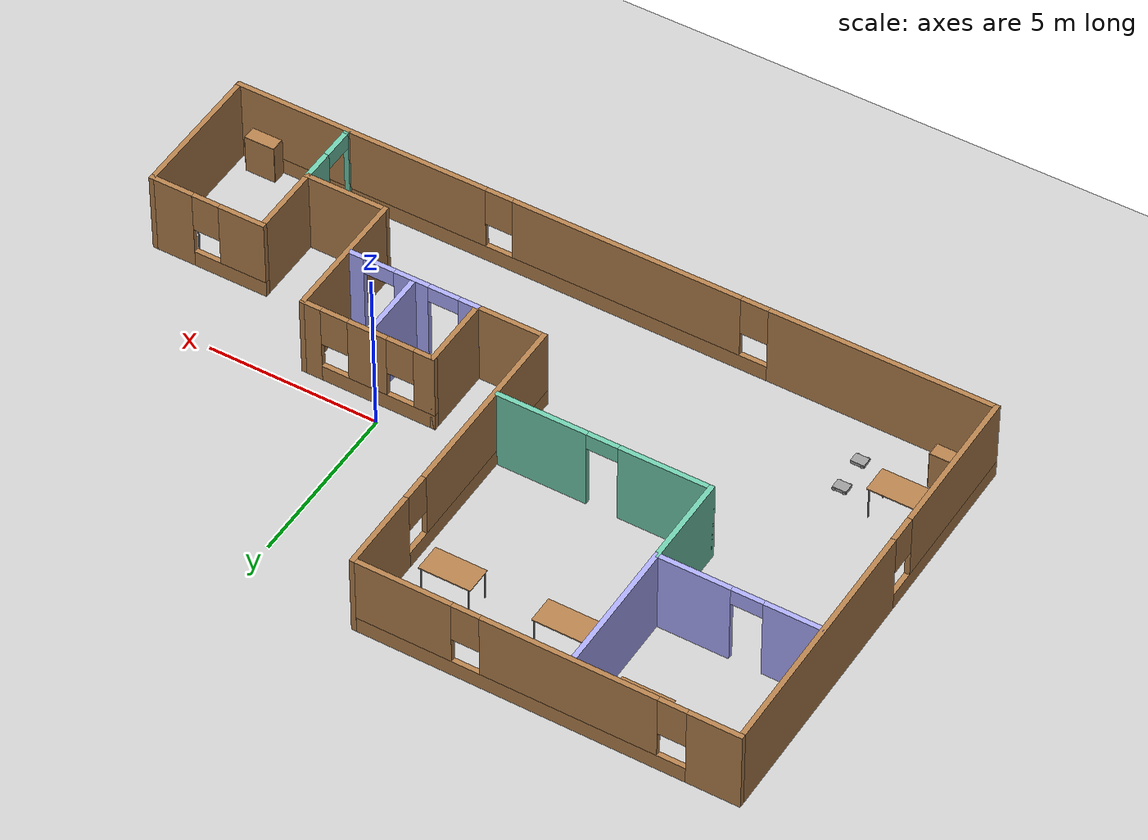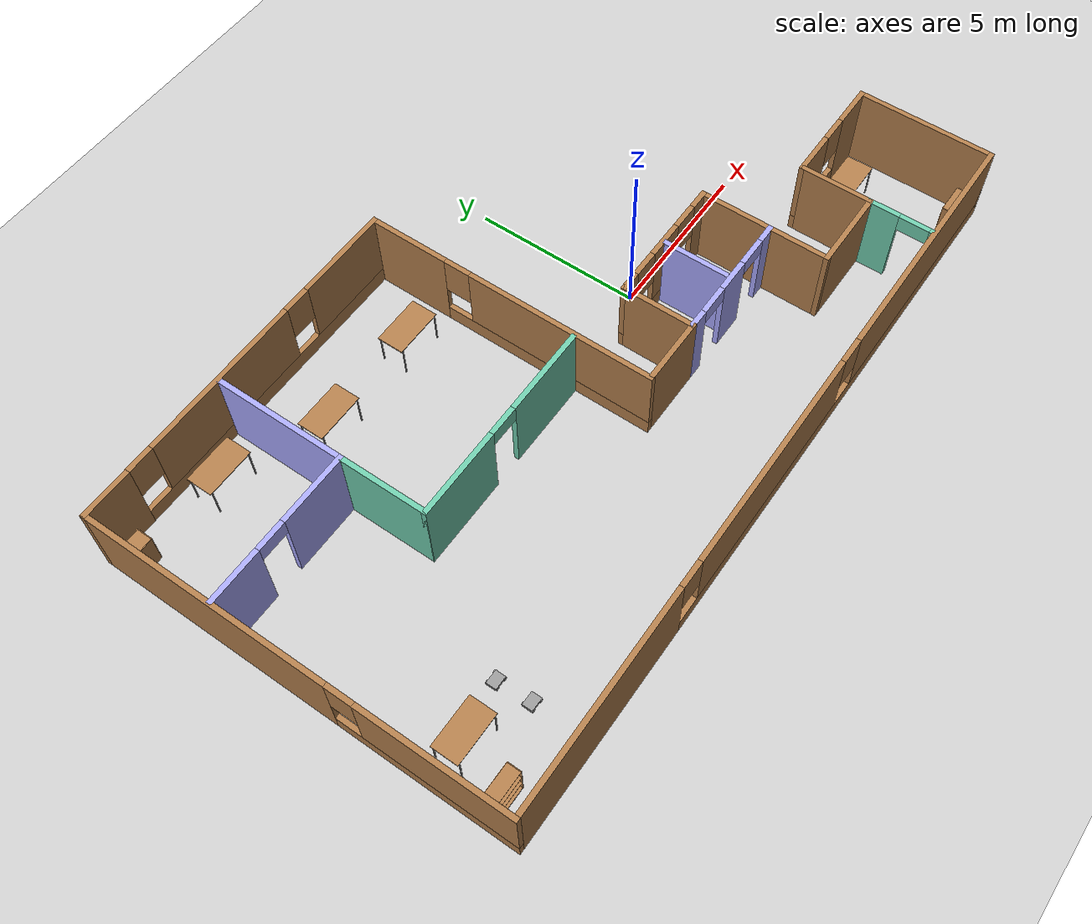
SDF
<sdf version="1.7">
 <world name="default">
  <plugin name="welcome" filename="libwelcome.so"/>
  <light name="sun" type="directional">
   <pose>0 0 10 0 -0 0</pose>
   <diffuse>0.8 0.8 0.8 1</diffuse>
   <specular>0.2 0.2 0.2 1</specular>
   <attenuation>
    <range>1000</range>
    <constant>0.9</constant>
    <linear>0.01</linear>
    <quadratic>0.001</quadratic>
   </attenuation>
   <direction>-0.5 0.1 -0.9</direction>
   <spot><inner_angle>0</inner_angle><outer_angle>0</outer_angle><falloff>0</falloff></spot>
  </light>
  <model name="ground_plane">
   <static>1</static>
   <link name="link">
    <collision name="collision">
     <geometry><plane><normal>0 0 1</normal><size>100 100</size></plane></geometry>
     <surface>
      <contact><collide_bitmask>65535</collide_bitmask></contact>
      <friction><ode><mu>100</mu><mu2>50</mu2></ode></friction>
     </surface>
    </collision>
    <visual name="visual">
     <cast_shadows>0</cast_shadows>
     <geometry><plane><normal>0 0 1</normal><size>100 100</size></plane></geometry>
     <material>
      <script><uri>file://media/materials/scripts/gazebo.material</uri><name>Gazebo/Grey</name></script>
     </material>
    </visual>
   </link>
  </model>
  <gravity>0 0 -9.8</gravity>
  <magnetic_field>6e-06 2.3e-05 -4.2e-05</magnetic_field>
  <atmosphere type="adiabatic"/>
  <physics type="ode">
   <max_step_size>0.001</max_step_size>
   <real_time_factor>1</real_time_factor>
   <real_time_update_rate>1000</real_time_update_rate>
  </physics>
  <scene><ambient>0.4 0.4 0.4 1</ambient><background>0.7 0.7 0.7 1</background><shadows>1</shadows></scene>
  <spherical_coordinates>
   <surface_model>EARTH_WGS84</surface_model>
   <latitude_deg>0</latitude_deg>
   <longitude_deg>0</longitude_deg>
   <elevation>0</elevation>
   <heading_deg>0</heading_deg>
  </spherical_coordinates>
  <model name="model">
   <pose>-2.971 -0.141859 0 0 -0 0</pose>
   <link name="Wall_1">
    <pose>-11.175 -0.000141 0 0 -0 -1.5708</pose>
    <visual name="Wall_1_Visual_0">
     <pose>-2.63427 0 1.25 0 -0 0</pose>
     <geometry><box><size>7.43146 0.15 2.5</size></box></geometry>
     <material>
      <script><uri>file://media/materials/scripts/gazebo.material</uri><name>Gazebo/Wood</name></script>
      <ambient>1 1 1 1</ambient>
     </material>
     <meta><layer>0</layer></meta>
    </visual>
    <collision name="Wall_1_Collision_0">
     <geometry><box><size>7.43146 0.15 2.5</size></box></geometry>
     <pose>-2.63427 0 1.25 0 -0 0</pose>
    </collision>
    <visual name="Wall_1_Visual_1">
     <pose>3.71573 0 0.25 0 -0 0</pose>
     <geometry><box><size>5.26854 0.15 0.5</size></box></geometry>
     <material>
      <script><uri>file://media/materials/scripts/gazebo.material</uri><name>Gazebo/Wood</name></script>
      <ambient>1 1 1 1</ambient>
     </material>
     <meta><layer>0</layer></meta>
    </visual>
    <collision name="Wall_1_Collision_1">
     <geometry><box><size>5.26854 0.15 0.5</size></box></geometry>
     <pose>3.71573 0 0.25 0 -0 0</pose>
    </collision>
    <visual name="Wall_1_Visual_2">
     <pose>4.11573 0 1.5 0 -0 0</pose>
     <geometry><box><size>4.46854 0.15 2</size></box></geometry>
     <material>
      <script><uri>file://media/materials/scripts/gazebo.material</uri><name>Gazebo/Wood</name></script>
      <ambient>1 1 1 1</ambient>
     </material>
     <meta><layer>0</layer></meta>
    </visual>
    <collision name="Wall_1_Collision_2">
     <geometry><box><size>4.46854 0.15 2</size></box></geometry>
     <pose>4.11573 0 1.5 0 -0 0</pose>
    </collision>
    <visual name="Wall_1_Visual_3">
     <pose>1.48146 0 1.9 0 -0 0</pose>
     <geometry><box><size>0.8 0.15 1.2</size></box></geometry>
     <material>
      <script><uri>file://media/materials/scripts/gazebo.material</uri><name>Gazebo/Wood</name></script>
      <ambient>1 1 1 1</ambient>
     </material>
     <meta><layer>0</layer></meta>
    </visual>
    <collision name="Wall_1_Collision_3">
     <geometry><box><size>0.8 0.15 1.2</size></box></geometry>
     <pose>1.48146 0 1.9 0 -0 0</pose>
    </collision>
   </link>
   <link name="Wall_10">
    <collision name="Wall_10_Collision">
     <geometry><box><size>2 0.15 2.5</size></box></geometry>
     <pose>0 0 1.25 0 -0 0</pose>
    </collision>
    <visual name="Wall_10_Visual">
     <pose>0 0 1.25 0 -0 0</pose>
     <geometry><box><size>2 0.15 2.5</size></box></geometry>
     <material>
      <script><uri>file://media/materials/scripts/gazebo.material</uri><name>Gazebo/Wood</name></script>
      <ambient>1 1 1 1</ambient>
     </material>
     <meta><layer>0</layer></meta>
    </visual>
    <pose>0.69978 -2.57513 0 0 -0 3.14158</pose>
   </link>
   <link name="Wall_19">
    <pose>-5.75 6.27486 0 0 -0 0</pose>
    <visual name="Wall_19_Visual_0">
     <pose>-4.73477 0 1.25 0 -0 0</pose>
     <geometry><box><size>1.53047 0.15 2.5</size></box></geometry>
     <material>
      <script><uri>file://media/materials/scripts/gazebo.material</uri><name>Gazebo/Wood</name></script>
      <ambient>1 1 1 1</ambient>
     </material>
     <meta><layer>0</layer></meta>
    </visual>
    <collision name="Wall_19_Collision_0">
     <geometry><box><size>1.53047 0.15 2.5</size></box></geometry>
     <pose>-4.73477 0 1.25 0 -0 0</pose>
    </collision>
    <visual name="Wall_19_Visual_1">
     <pose>0.765234 0 0.25 0 -0 0</pose>
     <geometry><box><size>9.46953 0.15 0.5</size></box></geometry>
     <material>
      <script><uri>file://media/materials/scripts/gazebo.material</uri><name>Gazebo/Wood</name></script>
      <ambient>1 1 1 1</ambient>
     </material>
     <meta><layer>0</layer></meta>
    </visual>
    <collision name="Wall_19_Collision_1">
     <geometry><box><size>9.46953 0.15 0.5</size></box></geometry>
     <pose>0.765234 0 0.25 0 -0 0</pose>
    </collision>
    <visual name="Wall_19_Visual_2">
     <pose>-0.67987 0 1.5 0 -0 0</pose>
     <geometry><box><size>4.97933 0.15 2</size></box></geometry>
     <material>
      <script><uri>file://media/materials/scripts/gazebo.material</uri><name>Gazebo/Wood</name></script>
      <ambient>1 1 1 1</ambient>
     </material>
     <meta><layer>0</layer></meta>
    </visual>
    <collision name="Wall_19_Collision_2">
     <geometry><box><size>4.97933 0.15 2</size></box></geometry>
     <pose>-0.67987 0 1.5 0 -0 0</pose>
    </collision>
    <visual name="Wall_19_Visual_3">
     <pose>4.0549 0 1.5 0 -0 0</pose>
     <geometry><box><size>2.89021 0.15 2</size></box></geometry>
     <material>
      <script><uri>file://media/materials/scripts/gazebo.material</uri><name>Gazebo/Wood</name></script>
      <ambient>1 1 1 1</ambient>
     </material>
     <meta><layer>0</layer></meta>
    </visual>
    <collision name="Wall_19_Collision_3">
     <geometry><box><size>2.89021 0.15 2</size></box></geometry>
     <pose>4.0549 0 1.5 0 -0 0</pose>
    </collision>
    <visual name="Wall_19_Visual_4">
     <pose>-3.56953 0 1.9 0 -0 0</pose>
     <geometry><box><size>0.8 0.15 1.2</size></box></geometry>
     <material>
      <script><uri>file://media/materials/scripts/gazebo.material</uri><name>Gazebo/Wood</name></script>
      <ambient>1 1 1 1</ambient>
     </material>
     <meta><layer>0</layer></meta>
    </visual>
    <collision name="Wall_19_Collision_4">
     <geometry><box><size>0.8 0.15 1.2</size></box></geometry>
     <pose>-3.56953 0 1.9 0 -0 0</pose>
    </collision>
    <visual name="Wall_19_Visual_5">
     <pose>2.20979 0 1.9 0 -0 0</pose>
     <geometry><box><size>0.8 0.15 1.2</size></box></geometry>
     <material>
      <script><uri>file://media/materials/scripts/gazebo.material</uri><name>Gazebo/Wood</name></script>
      <ambient>1 1 1 1</ambient>
     </material>
     <meta><layer>0</layer></meta>
    </visual>
    <collision name="Wall_19_Collision_5">
     <geometry><box><size>0.8 0.15 1.2</size></box></geometry>
     <pose>2.20979 0 1.9 0 -0 0</pose>
    </collision>
   </link>
   <link name="Wall_2">
    <pose>0 -6.27514 0 0 -0 0</pose>
    <visual name="Wall_2_Visual_0">
     <pose>-7.97532 0 1.25 0 -0 0</pose>
     <geometry><box><size>6.54936 0.15 2.5</size></box></geometry>
     <material>
      <script><uri>file://media/materials/scripts/gazebo.material</uri><name>Gazebo/Wood</name></script>
      <ambient>1 1 1 1</ambient>
     </material>
     <meta><layer>0</layer></meta>
    </visual>
    <collision name="Wall_2_Collision_0">
     <geometry><box><size>6.54936 0.15 2.5</size></box></geometry>
     <pose>-7.97532 0 1.25 0 -0 0</pose>
    </collision>
    <visual name="Wall_2_Visual_1">
     <pose>3.27468 0 0.25 0 -0 0</pose>
     <geometry><box><size>15.9506 0.15 0.5</size></box></geometry>
     <material>
      <script><uri>file://media/materials/scripts/gazebo.material</uri><name>Gazebo/Wood</name></script>
      <ambient>1 1 1 1</ambient>
     </material>
     <meta><layer>0</layer></meta>
    </visual>
    <collision name="Wall_2_Collision_1">
     <geometry><box><size>15.9506 0.15 0.5</size></box></geometry>
     <pose>3.27468 0 0.25 0 -0 0</pose>
    </collision>
    <visual name="Wall_2_Visual_2">
     <pose>-0.528875 0 1.5 0 -0 0</pose>
     <geometry><box><size>6.74354 0.15 2</size></box></geometry>
     <material>
      <script><uri>file://media/materials/scripts/gazebo.material</uri><name>Gazebo/Wood</name></script>
      <ambient>1 1 1 1</ambient>
     </material>
     <meta><layer>0</layer></meta>
    </visual>
    <collision name="Wall_2_Collision_2">
     <geometry><box><size>6.74354 0.15 2</size></box></geometry>
     <pose>-0.528875 0 1.5 0 -0 0</pose>
    </collision>
    <visual name="Wall_2_Visual_3">
     <pose>7.44645 0 1.5 0 -0 0</pose>
     <geometry><box><size>7.6071 0.15 2</size></box></geometry>
     <material>
      <script><uri>file://media/materials/scripts/gazebo.material</uri><name>Gazebo/Wood</name></script>
      <ambient>1 1 1 1</ambient>
     </material>
     <meta><layer>0</layer></meta>
    </visual>
    <collision name="Wall_2_Collision_3">
     <geometry><box><size>7.6071 0.15 2</size></box></geometry>
     <pose>7.44645 0 1.5 0 -0 0</pose>
    </collision>
    <visual name="Wall_2_Visual_4">
     <pose>-4.30065 0 1.9 0 -0 0</pose>
     <geometry><box><size>0.8 0.15 1.2</size></box></geometry>
     <material>
      <script><uri>file://media/materials/scripts/gazebo.material</uri><name>Gazebo/Wood</name></script>
      <ambient>1 1 1 1</ambient>
     </material>
     <meta><layer>0</layer></meta>
    </visual>
    <collision name="Wall_2_Collision_4">
     <geometry><box><size>0.8 0.15 1.2</size></box></geometry>
     <pose>-4.30065 0 1.9 0 -0 0</pose>
    </collision>
    <visual name="Wall_2_Visual_5">
     <pose>3.24289 0 1.9 0 -0 0</pose>
     <geometry><box><size>0.8 0.15 1.2</size></box></geometry>
     <material>
      <script><uri>file://media/materials/scripts/gazebo.material</uri><name>Gazebo/Wood</name></script>
      <ambient>1 1 1 1</ambient>
     </material>
     <meta><layer>0</layer></meta>
    </visual>
    <collision name="Wall_2_Collision_5">
     <geometry><box><size>0.8 0.15 1.2</size></box></geometry>
     <pose>3.24289 0 1.9 0 -0 0</pose>
    </collision>
   </link>
   <link name="Wall_20">
    <pose>-0.325 1.84986 0 0 -0 -1.5708</pose>
    <visual name="Wall_20_Visual_0">
     <pose>-3.26344 0 1.25 0 -0 0</pose>
     <geometry><box><size>2.47369 0.15 2.5</size></box></geometry>
     <material>
      <script><uri>file://media/materials/scripts/gazebo.material</uri><name>Gazebo/Wood</name></script>
      <ambient>1 1 1 1</ambient>
     </material>
     <meta><layer>0</layer></meta>
    </visual>
    <collision name="Wall_20_Collision_0">
     <geometry><box><size>2.47369 0.15 2.5</size></box></geometry>
     <pose>-3.26344 0 1.25 0 -0 0</pose>
    </collision>
    <visual name="Wall_20_Visual_1">
     <pose>1.23685 0 0.25 0 -0 0</pose>
     <geometry><box><size>6.52687 0.15 0.5</size></box></geometry>
     <material>
      <script><uri>file://media/materials/scripts/gazebo.material</uri><name>Gazebo/Wood</name></script>
      <ambient>1 1 1 1</ambient>
     </material>
     <meta><layer>0</layer></meta>
    </visual>
    <collision name="Wall_20_Collision_1">
     <geometry><box><size>6.52687 0.15 0.5</size></box></geometry>
     <pose>1.23685 0 0.25 0 -0 0</pose>
    </collision>
    <visual name="Wall_20_Visual_2">
     <pose>1.63685 0 1.5 0 -0 0</pose>
     <geometry><box><size>5.72687 0.15 2</size></box></geometry>
     <material>
      <script><uri>file://media/materials/scripts/gazebo.material</uri><name>Gazebo/Wood</name></script>
      <ambient>1 1 1 1</ambient>
     </material>
     <meta><layer>0</layer></meta>
    </visual>
    <collision name="Wall_20_Collision_2">
     <geometry><box><size>5.72687 0.15 2</size></box></geometry>
     <pose>1.63685 0 1.5 0 -0 0</pose>
    </collision>
    <visual name="Wall_20_Visual_3">
     <pose>-1.62659 0 1.9 0 -0 0</pose>
     <geometry><box><size>0.8 0.15 1.2</size></box></geometry>
     <material>
      <script><uri>file://media/materials/scripts/gazebo.material</uri><name>Gazebo/Wood</name></script>
      <ambient>1 1 1 1</ambient>
     </material>
     <meta><layer>0</layer></meta>
    </visual>
    <collision name="Wall_20_Collision_3">
     <geometry><box><size>0.8 0.15 1.2</size></box></geometry>
     <pose>-1.62659 0 1.9 0 -0 0</pose>
    </collision>
   </link>
   <link name="Wall_22">
    <pose>7.825 -5.25014 0 0 -0 -1.5708</pose>
    <visual name="Wall_22_Visual_0">
     <pose>-0.510461 0 1.25 0 -0 0</pose>
     <geometry><box><size>0.979077 0.15 2.5</size></box></geometry>
     <material>
      <script><uri>file://media/materials/scripts/gazebo.material</uri><name>Gazebo/Grey</name></script>
      <ambient>0.435294 0.796078 0.67451 1</ambient>
     </material>
     <meta><layer>0</layer></meta>
    </visual>
    <collision name="Wall_22_Collision_0">
     <geometry><box><size>0.979077 0.15 2.5</size></box></geometry>
     <pose>-0.510461 0 1.25 0 -0 0</pose>
    </collision>
    <visual name="Wall_22_Visual_1">
     <pose>0.939539 0 1.25 0 -0 0</pose>
     <geometry><box><size>0.120923 0.15 2.5</size></box></geometry>
     <material>
      <script><uri>file://media/materials/scripts/gazebo.material</uri><name>Gazebo/Grey</name></script>
      <ambient>0.435294 0.796078 0.67451 1</ambient>
     </material>
     <meta><layer>0</layer></meta>
    </visual>
    <collision name="Wall_22_Collision_1">
     <geometry><box><size>0.120923 0.15 2.5</size></box></geometry>
     <pose>0.939539 0 1.25 0 -0 0</pose>
    </collision>
    <visual name="Wall_22_Visual_2">
     <pose>0.429077 0 2.25 0 -0 0</pose>
     <geometry><box><size>0.9 0.15 0.5</size></box></geometry>
     <material>
      <script><uri>file://media/materials/scripts/gazebo.material</uri><name>Gazebo/Grey</name></script>
      <ambient>0.435294 0.796078 0.67451 1</ambient>
     </material>
     <meta><layer>0</layer></meta>
    </visual>
    <collision name="Wall_22_Collision_2">
     <geometry><box><size>0.9 0.15 0.5</size></box></geometry>
     <pose>0.429077 0 2.25 0 -0 0</pose>
    </collision>
   </link>
   <link name="Wall_25">
    <collision name="Wall_25_Collision">
     <geometry><box><size>4 0.15 2.5</size></box></geometry>
     <pose>0 0 1.25 0 -0 0</pose>
    </collision>
    <visual name="Wall_25_Visual">
     <pose>0 0 1.25 0 -0 0</pose>
     <geometry><box><size>4 0.15 2.5</size></box></geometry>
     <material>
      <script><uri>file://media/materials/scripts/gazebo.material</uri><name>Gazebo/Grey</name></script>
      <ambient>0.666667 0.666667 1 1</ambient>
     </material>
     <meta><layer>0</layer></meta>
    </visual>
    <pose>-6.52178 4.25874 0 0 -0 -1.57091</pose>
   </link>
   <link name="Wall_26">
    <pose>-8.82178 2.33374 0 0 -0 -3.14154</pose>
    <visual name="Wall_26_Visual_0">
     <pose>-1.28498 0 1.25 0 -0 0</pose>
     <geometry><box><size>2.18005 0.15 2.5</size></box></geometry>
     <material>
      <script><uri>file://media/materials/scripts/gazebo.material</uri><name>Gazebo/Grey</name></script>
      <ambient>0.666667 0.666667 1 1</ambient>
     </material>
     <meta><layer>0</layer></meta>
    </visual>
    <collision name="Wall_26_Collision_0">
     <geometry><box><size>2.18005 0.15 2.5</size></box></geometry>
     <pose>-1.28498 0 1.25 0 -0 0</pose>
    </collision>
    <visual name="Wall_26_Visual_1">
     <pose>1.54002 0 1.25 0 -0 0</pose>
     <geometry><box><size>1.66995 0.15 2.5</size></box></geometry>
     <material>
      <script><uri>file://media/materials/scripts/gazebo.material</uri><name>Gazebo/Grey</name></script>
      <ambient>0.666667 0.666667 1 1</ambient>
     </material>
     <meta><layer>0</layer></meta>
    </visual>
    <collision name="Wall_26_Collision_1">
     <geometry><box><size>1.66995 0.15 2.5</size></box></geometry>
     <pose>1.54002 0 1.25 0 -0 0</pose>
    </collision>
    <visual name="Wall_26_Visual_2">
     <pose>0.255046 0 2.25 0 -0 0</pose>
     <geometry><box><size>0.9 0.15 0.5</size></box></geometry>
     <material>
      <script><uri>file://media/materials/scripts/gazebo.material</uri><name>Gazebo/Grey</name></script>
      <ambient>0.666667 0.666667 1 1</ambient>
     </material>
     <meta><layer>0</layer></meta>
    </visual>
    <collision name="Wall_26_Collision_2">
     <geometry><box><size>0.9 0.15 0.5</size></box></geometry>
     <pose>0.255046 0 2.25 0 -0 0</pose>
    </collision>
   </link>
   <link name="Wall_28">
    <collision name="Wall_28_Collision">
     <geometry><box><size>2.75 0.15 2.5</size></box></geometry>
     <pose>0 0 1.25 0 -0 0</pose>
    </collision>
    <visual name="Wall_28_Visual">
     <pose>0 0 1.25 0 -0 0</pose>
     <geometry><box><size>2.75 0.15 2.5</size></box></geometry>
     <material>
      <script><uri>file://media/materials/scripts/gazebo.material</uri><name>Gazebo/Grey</name></script>
      <ambient>0.435294 0.796078 0.67451 1</ambient>
     </material>
     <meta><layer>0</layer></meta>
    </visual>
    <pose>-6.522 1.03386 0 0 -0 -1.5708</pose>
   </link>
   <link name="Wall_29">
    <pose>-3.472 -0.266141 0 0 -0 0</pose>
    <visual name="Wall_29_Visual_0">
     <pose>-1.77642 0 1.25 0 -0 0</pose>
     <geometry><box><size>2.69717 0.15 2.5</size></box></geometry>
     <material>
      <script><uri>file://media/materials/scripts/gazebo.material</uri><name>Gazebo/Grey</name></script>
      <ambient>0.435294 0.796078 0.67451 1</ambient>
     </material>
     <meta><layer>0</layer></meta>
    </visual>
    <collision name="Wall_29_Collision_0">
     <geometry><box><size>2.69717 0.15 2.5</size></box></geometry>
     <pose>-1.77642 0 1.25 0 -0 0</pose>
    </collision>
    <visual name="Wall_29_Visual_1">
     <pose>1.79858 0 1.25 0 -0 0</pose>
     <geometry><box><size>2.65283 0.15 2.5</size></box></geometry>
     <material>
      <script><uri>file://media/materials/scripts/gazebo.material</uri><name>Gazebo/Grey</name></script>
      <ambient>0.435294 0.796078 0.67451 1</ambient>
     </material>
     <meta><layer>0</layer></meta>
    </visual>
    <collision name="Wall_29_Collision_1">
     <geometry><box><size>2.65283 0.15 2.5</size></box></geometry>
     <pose>1.79858 0 1.25 0 -0 0</pose>
    </collision>
    <visual name="Wall_29_Visual_2">
     <pose>0.022167 0 2.25 0 -0 0</pose>
     <geometry><box><size>0.9 0.15 0.5</size></box></geometry>
     <material>
      <script><uri>file://media/materials/scripts/gazebo.material</uri><name>Gazebo/Grey</name></script>
      <ambient>0.435294 0.796078 0.67451 1</ambient>
     </material>
     <meta><layer>0</layer></meta>
    </visual>
    <collision name="Wall_29_Collision_2">
     <geometry><box><size>0.9 0.15 0.5</size></box></geometry>
     <pose>0.022167 0 2.25 0 -0 0</pose>
    </collision>
   </link>
   <link name="Wall_3">
    <collision name="Wall_3_Collision">
     <geometry><box><size>4.2 0.15 2.5</size></box></geometry>
     <pose>0 0 1.25 0 -0 0</pose>
    </collision>
    <visual name="Wall_3_Visual">
     <pose>0 0 1.25 0 -0 0</pose>
     <geometry><box><size>4.2 0.15 2.5</size></box></geometry>
     <material>
      <script><uri>file://media/materials/scripts/gazebo.material</uri><name>Gazebo/Wood</name></script>
      <ambient>1 1 1 1</ambient>
     </material>
     <meta><layer>0</layer></meta>
    </visual>
    <pose>11.175 -4.25014 0 0 -0 1.5708</pose>
   </link>
   <link name="Wall_31">
    <pose>3.54978 -2.57513 0 0 -0 5e-06</pose>
    <visual name="Wall_31_Visual_0">
     <pose>-1.69788 0 1.25 0 -0 0</pose>
     <geometry><box><size>0.604236 0.15 2.5</size></box></geometry>
     <material>
      <script><uri>file://media/materials/scripts/gazebo.material</uri><name>Gazebo/Grey</name></script>
      <ambient>0.666667 0.666667 1 1</ambient>
     </material>
     <meta><layer>0</layer></meta>
    </visual>
    <collision name="Wall_31_Collision_0">
     <geometry><box><size>0.604236 0.15 2.5</size></box></geometry>
     <pose>-1.69788 0 1.25 0 -0 0</pose>
    </collision>
    <visual name="Wall_31_Visual_1">
     <pose>0.012277 0 1.25 0 -0 0</pose>
     <geometry><box><size>1.01608 0.15 2.5</size></box></geometry>
     <material>
      <script><uri>file://media/materials/scripts/gazebo.material</uri><name>Gazebo/Grey</name></script>
      <ambient>0.666667 0.666667 1 1</ambient>
     </material>
     <meta><layer>0</layer></meta>
    </visual>
    <collision name="Wall_31_Collision_1">
     <geometry><box><size>1.01608 0.15 2.5</size></box></geometry>
     <pose>0.012277 0 1.25 0 -0 0</pose>
    </collision>
    <visual name="Wall_31_Visual_2">
     <pose>1.71016 0 1.25 0 -0 0</pose>
     <geometry><box><size>0.579681 0.15 2.5</size></box></geometry>
     <material>
      <script><uri>file://media/materials/scripts/gazebo.material</uri><name>Gazebo/Grey</name></script>
      <ambient>0.666667 0.666667 1 1</ambient>
     </material>
     <meta><layer>0</layer></meta>
    </visual>
    <collision name="Wall_31_Collision_2">
     <geometry><box><size>0.579681 0.15 2.5</size></box></geometry>
     <pose>1.71016 0 1.25 0 -0 0</pose>
    </collision>
    <visual name="Wall_31_Visual_3">
     <pose>-0.945764 0 2.25 0 -0 0</pose>
     <geometry><box><size>0.9 0.15 0.5</size></box></geometry>
     <material>
      <script><uri>file://media/materials/scripts/gazebo.material</uri><name>Gazebo/Grey</name></script>
      <ambient>0.666667 0.666667 1 1</ambient>
     </material>
     <meta><layer>0</layer></meta>
    </visual>
    <collision name="Wall_31_Collision_3">
     <geometry><box><size>0.9 0.15 0.5</size></box></geometry>
     <pose>-0.945764 0 2.25 0 -0 0</pose>
    </collision>
    <visual name="Wall_31_Visual_4">
     <pose>0.970319 0 2.25 0 -0 0</pose>
     <geometry><box><size>0.9 0.15 0.5</size></box></geometry>
     <material>
      <script><uri>file://media/materials/scripts/gazebo.material</uri><name>Gazebo/Grey</name></script>
      <ambient>0.666667 0.666667 1 1</ambient>
     </material>
     <meta><layer>0</layer></meta>
    </visual>
    <collision name="Wall_31_Collision_4">
     <geometry><box><size>0.9 0.15 0.5</size></box></geometry>
     <pose>0.970319 0 2.25 0 -0 0</pose>
    </collision>
   </link>
   <link name="Wall_33">
    <collision name="Wall_33_Collision">
     <geometry><box><size>2 0.15 2.5</size></box></geometry>
     <pose>0 0 1.25 0 -0 0</pose>
    </collision>
    <visual name="Wall_33_Visual">
     <pose>0 0 1.25 0 -0 0</pose>
     <geometry><box><size>2 0.15 2.5</size></box></geometry>
     <material>
      <script><uri>file://media/materials/scripts/gazebo.material</uri><name>Gazebo/Grey</name></script>
      <ambient>0.666667 0.666667 1 1</ambient>
     </material>
     <meta><layer>0</layer></meta>
    </visual>
    <pose>3.48579 -1.49406 0 0 -0 -1.5708</pose>
   </link>
   <link name="Wall_4">
    <pose>9.5 -2.22514 0 0 -0 3.14159</pose>
    <visual name="Wall_4_Visual_0">
     <pose>-1.09466 0 1.25 0 -0 0</pose>
     <geometry><box><size>1.31068 0.15 2.5</size></box></geometry>
     <material>
      <script><uri>file://media/materials/scripts/gazebo.material</uri><name>Gazebo/Wood</name></script>
      <ambient>1 1 1 1</ambient>
     </material>
     <meta><layer>0</layer></meta>
    </visual>
    <collision name="Wall_4_Collision_0">
     <geometry><box><size>1.31068 0.15 2.5</size></box></geometry>
     <pose>-1.09466 0 1.25 0 -0 0</pose>
    </collision>
    <visual name="Wall_4_Visual_1">
     <pose>0.655341 0 0.25 0 -0 0</pose>
     <geometry><box><size>2.18932 0.15 0.5</size></box></geometry>
     <material>
      <script><uri>file://media/materials/scripts/gazebo.material</uri><name>Gazebo/Wood</name></script>
      <ambient>1 1 1 1</ambient>
     </material>
     <meta><layer>0</layer></meta>
    </visual>
    <collision name="Wall_4_Collision_1">
     <geometry><box><size>2.18932 0.15 0.5</size></box></geometry>
     <pose>0.655341 0 0.25 0 -0 0</pose>
    </collision>
    <visual name="Wall_4_Visual_2">
     <pose>1.05534 0 1.5 0 -0 0</pose>
     <geometry><box><size>1.38932 0.15 2</size></box></geometry>
     <material>
      <script><uri>file://media/materials/scripts/gazebo.material</uri><name>Gazebo/Wood</name></script>
      <ambient>1 1 1 1</ambient>
     </material>
     <meta><layer>0</layer></meta>
    </visual>
    <collision name="Wall_4_Collision_2">
     <geometry><box><size>1.38932 0.15 2</size></box></geometry>
     <pose>1.05534 0 1.5 0 -0 0</pose>
    </collision>
    <visual name="Wall_4_Visual_3">
     <pose>-0.039318 0 1.9 0 -0 0</pose>
     <geometry><box><size>0.8 0.15 1.2</size></box></geometry>
     <material>
      <script><uri>file://media/materials/scripts/gazebo.material</uri><name>Gazebo/Wood</name></script>
      <ambient>1 1 1 1</ambient>
     </material>
     <meta><layer>0</layer></meta>
    </visual>
    <collision name="Wall_4_Collision_3">
     <geometry><box><size>0.8 0.15 1.2</size></box></geometry>
     <pose>-0.039318 0 1.9 0 -0 0</pose>
    </collision>
   </link>
   <link name="Wall_5">
    <collision name="Wall_5_Collision">
     <geometry><box><size>2.25 0.15 2.5</size></box></geometry>
     <pose>0 0 1.25 0 -0 0</pose>
    </collision>
    <visual name="Wall_5_Visual">
     <pose>0 0 1.25 0 -0 0</pose>
     <geometry><box><size>2.25 0.15 2.5</size></box></geometry>
     <material>
      <script><uri>file://media/materials/scripts/gazebo.material</uri><name>Gazebo/Wood</name></script>
      <ambient>1 1 1 1</ambient>
     </material>
     <meta><layer>0</layer></meta>
    </visual>
    <pose>7.825 -3.27514 0 0 -0 -1.5708</pose>
   </link>
   <link name="Wall_6">
    <collision name="Wall_6_Collision">
     <geometry><box><size>2.5 0.15 2.5</size></box></geometry>
     <pose>0 0 1.25 0 -0 0</pose>
    </collision>
    <visual name="Wall_6_Visual">
     <pose>0 0 1.25 0 -0 0</pose>
     <geometry><box><size>2.5 0.15 2.5</size></box></geometry>
     <material>
      <script><uri>file://media/materials/scripts/gazebo.material</uri><name>Gazebo/Wood</name></script>
      <ambient>1 1 1 1</ambient>
     </material>
     <meta><layer>0</layer></meta>
    </visual>
    <pose>6.65 -4.32514 0 0 -0 3.14159</pose>
   </link>
   <link name="Wall_7">
    <collision name="Wall_7_Collision">
     <geometry><box><size>4 0.15 2.5</size></box></geometry>
     <pose>0 0 1.25 0 -0 0</pose>
    </collision>
    <visual name="Wall_7_Visual">
     <pose>0 0 1.25 0 -0 0</pose>
     <geometry><box><size>4 0.15 2.5</size></box></geometry>
     <material>
      <script><uri>file://media/materials/scripts/gazebo.material</uri><name>Gazebo/Wood</name></script>
      <ambient>1 1 1 1</ambient>
     </material>
     <meta><layer>0</layer></meta>
    </visual>
    <pose>5.475 -2.40014 0 0 -0 1.5708</pose>
   </link>
   <link name="Wall_8">
    <pose>3.55 -0.475141 0 0 -0 3.14159</pose>
    <visual name="Wall_8_Visual_0">
     <pose>-1.68521 0 1.25 0 -0 0</pose>
     <geometry><box><size>0.62957 0.15 2.5</size></box></geometry>
     <material>
      <script><uri>file://media/materials/scripts/gazebo.material</uri><name>Gazebo/Wood</name></script>
      <ambient>1 1 1 1</ambient>
     </material>
     <meta><layer>0</layer></meta>
    </visual>
    <collision name="Wall_8_Collision_0">
     <geometry><box><size>0.62957 0.15 2.5</size></box></geometry>
     <pose>-1.68521 0 1.25 0 -0 0</pose>
    </collision>
    <visual name="Wall_8_Visual_1">
     <pose>0.314785 0 0.25 0 -0 0</pose>
     <geometry><box><size>3.37043 0.15 0.5</size></box></geometry>
     <material>
      <script><uri>file://media/materials/scripts/gazebo.material</uri><name>Gazebo/Wood</name></script>
      <ambient>1 1 1 1</ambient>
     </material>
     <meta><layer>0</layer></meta>
    </visual>
    <collision name="Wall_8_Collision_1">
     <geometry><box><size>3.37043 0.15 0.5</size></box></geometry>
     <pose>0.314785 0 0.25 0 -0 0</pose>
    </collision>
    <visual name="Wall_8_Visual_2">
     <pose>0.00293 0 1.5 0 -0 0</pose>
     <geometry><box><size>1.14672 0.15 2</size></box></geometry>
     <material>
      <script><uri>file://media/materials/scripts/gazebo.material</uri><name>Gazebo/Wood</name></script>
      <ambient>1 1 1 1</ambient>
     </material>
     <meta><layer>0</layer></meta>
    </visual>
    <collision name="Wall_8_Collision_2">
     <geometry><box><size>1.14672 0.15 2</size></box></geometry>
     <pose>0.00293 0 1.5 0 -0 0</pose>
    </collision>
    <visual name="Wall_8_Visual_3">
     <pose>1.68815 0 1.5 0 -0 0</pose>
     <geometry><box><size>0.62371 0.15 2</size></box></geometry>
     <material>
      <script><uri>file://media/materials/scripts/gazebo.material</uri><name>Gazebo/Wood</name></script>
      <ambient>1 1 1 1</ambient>
     </material>
     <meta><layer>0</layer></meta>
    </visual>
    <collision name="Wall_8_Collision_3">
     <geometry><box><size>0.62371 0.15 2</size></box></geometry>
     <pose>1.68815 0 1.5 0 -0 0</pose>
    </collision>
    <visual name="Wall_8_Visual_4">
     <pose>-0.97043 0 1.9 0 -0 0</pose>
     <geometry><box><size>0.8 0.15 1.2</size></box></geometry>
     <material>
      <script><uri>file://media/materials/scripts/gazebo.material</uri><name>Gazebo/Wood</name></script>
      <ambient>1 1 1 1</ambient>
     </material>
     <meta><layer>0</layer></meta>
    </visual>
    <collision name="Wall_8_Collision_4">
     <geometry><box><size>0.8 0.15 1.2</size></box></geometry>
     <pose>-0.97043 0 1.9 0 -0 0</pose>
    </collision>
    <visual name="Wall_8_Visual_5">
     <pose>0.97629 0 1.9 0 -0 0</pose>
     <geometry><box><size>0.8 0.15 1.2</size></box></geometry>
     <material>
      <script><uri>file://media/materials/scripts/gazebo.material</uri><name>Gazebo/Wood</name></script>
      <ambient>1 1 1 1</ambient>
     </material>
     <meta><layer>0</layer></meta>
    </visual>
    <collision name="Wall_8_Collision_5">
     <geometry><box><size>0.8 0.15 1.2</size></box></geometry>
     <pose>0.97629 0 1.9 0 -0 0</pose>
    </collision>
   </link>
   <link name="Wall_9">
    <collision name="Wall_9_Collision">
     <geometry><box><size>2.25 0.15 2.5</size></box></geometry>
     <pose>0 0 1.25 0 -0 0</pose>
    </collision>
    <visual name="Wall_9_Visual">
     <pose>0 0 1.25 0 -0 0</pose>
     <geometry><box><size>2.25 0.15 2.5</size></box></geometry>
     <material>
      <script><uri>file://media/materials/scripts/gazebo.material</uri><name>Gazebo/Wood</name></script>
      <ambient>1 1 1 1</ambient>
     </material>
     <meta><layer>0</layer></meta>
    </visual>
    <pose>1.625 -1.52514 0 0 -0 -1.5708</pose>
   </link>
   <static>1</static>
  </model>
  <model name="model_2">
   <link name="link_0">
    <inertial>
     <mass>1</mass>
     <inertia>
      <ixx>0.166667</ixx>
      <ixy>0</ixy>
      <ixz>0</ixz>
      <iyy>0.166667</iyy>
      <iyz>0</iyz>
      <izz>0.166667</izz>
     </inertia>
    </inertial>
    <pose>0 -2e-06 0 0 -0 0</pose>
    <visual name="visual">
     <geometry><box><size>0.4 0.3 0.1</size></box></geometry>
     <material>
      <lighting>1</lighting>
      <script><uri>file://media/materials/scripts/gazebo.material</uri><name>Gazebo/Grey</name></script>
      <shader type="pixel"><normal_map>__default__</normal_map></shader>
      <ambient>0.3 0.3 0.3 1</ambient>
      <diffuse>0.7 0.7 0.7 1</diffuse>
      <specular>0.01 0.01 0.01 1</specular>
      <emissive>0 0 0 1</emissive>
     </material>
    </visual>
    <collision name="collision">
     <geometry><box><size>0.4 0.3 0.1</size></box></geometry>
     <surface>
      <friction>
       <ode><mu>1</mu><mu2>1</mu2><fdir1>0 0 0</fdir1><slip1>0</slip1><slip2>0</slip2></ode>
       <torsional>
        <coefficient>1</coefficient>
        <patch_radius>0</patch_radius>
        <surface_radius>0</surface_radius>
        <use_patch_radius>1</use_patch_radius>
        <ode><slip>0</slip></ode>
       </torsional>
      </friction>
      <bounce><restitution_coefficient>0</restitution_coefficient><threshold>1e+06</threshold></bounce>
      <contact>
       <collide_without_contact>0</collide_without_contact>
       <collide_without_contact_bitmask>1</collide_without_contact_bitmask>
       <collide_bitmask>1</collide_bitmask>
       <ode>
        <soft_cfm>0</soft_cfm>
        <soft_erp>0.2</soft_erp>
        <kp>1e+13</kp>
        <kd>1</kd>
        <max_vel>0.01</max_vel>
        <min_depth>0</min_depth>
       </ode>
       <bullet>
        <split_impulse>1</split_impulse>
        <split_impulse_penetration_threshold>-0.01</split_impulse_penetration_threshold>
        <soft_cfm>0</soft_cfm>
        <soft_erp>0.2</soft_erp>
        <kp>1e+13</kp>
        <kd>1</kd>
       </bullet>
      </contact>
     </surface>
    </collision>
   </link>
   <link name="link_0_clone">
    <inertial>
     <mass>1</mass>
     <inertia>
      <ixx>0.166667</ixx>
      <ixy>0</ixy>
      <ixz>0</ixz>
      <iyy>0.166667</iyy>
      <iyz>0</iyz>
      <izz>0.166667</izz>
     </inertia>
    </inertial>
    <pose>0.052453 -1.00786 0 0 -0 0</pose>
    <visual name="visual">
     <geometry><box><size>0.4 0.3 0.1</size></box></geometry>
     <material>
      <lighting>1</lighting>
      <script><uri>file://media/materials/scripts/gazebo.material</uri><name>Gazebo/Grey</name></script>
      <shader type="pixel"><normal_map>__default__</normal_map></shader>
      <ambient>0.3 0.3 0.3 1</ambient>
      <diffuse>0.7 0.7 0.7 1</diffuse>
      <specular>0.01 0.01 0.01 1</specular>
      <emissive>0 0 0 1</emissive>
     </material>
    </visual>
    <collision name="collision">
     <geometry><box><size>0.4 0.3 0.1</size></box></geometry>
     <surface>
      <friction>
       <ode><mu>1</mu><mu2>1</mu2><fdir1>0 0 0</fdir1><slip1>0</slip1><slip2>0</slip2></ode>
       <torsional>
        <coefficient>1</coefficient>
        <patch_radius>0</patch_radius>
        <surface_radius>0</surface_radius>
        <use_patch_radius>1</use_patch_radius>
        <ode><slip>0</slip></ode>
       </torsional>
      </friction>
      <bounce><restitution_coefficient>0</restitution_coefficient><threshold>1e+06</threshold></bounce>
      <contact>
       <collide_without_contact>0</collide_without_contact>
       <collide_without_contact_bitmask>1</collide_without_contact_bitmask>
       <collide_bitmask>1</collide_bitmask>
       <ode>
        <soft_cfm>0</soft_cfm>
        <soft_erp>0.2</soft_erp>
        <kp>1e+13</kp>
        <kd>1</kd>
        <max_vel>0.01</max_vel>
        <min_depth>0</min_depth>
       </ode>
       <bullet>
        <split_impulse>1</split_impulse>
        <split_impulse_penetration_threshold>-0.01</split_impulse_penetration_threshold>
        <soft_cfm>0</soft_cfm>
        <soft_erp>0.2</soft_erp>
        <kp>1e+13</kp>
        <kd>1</kd>
       </bullet>
      </contact>
     </surface>
    </collision>
   </link>
   <link name="link_1">
    <inertial>
     <mass>1</mass>
     <inertia><ixx>0.145833</ixx><ixy>0</ixy><ixz>0</ixz><iyy>0.145833</iyy><iyz>0</iyz><izz>0.125</izz></inertia>
    </inertial>
    <pose>-0.149999 -0.160015 0 1.5707 -0 0</pose>
    <visual name="visual">
     <geometry><cylinder><radius>0.05</radius><length>0.02</length></cylinder></geometry>
     <material>
      <lighting>1</lighting>
      <script><uri>file://media/materials/scripts/gazebo.material</uri><name>Gazebo/Grey</name></script>
      <shader type="pixel"><normal_map>__default__</normal_map></shader>
      <ambient>0.3 0.3 0.3 1</ambient>
      <diffuse>0.7 0.7 0.7 1</diffuse>
      <specular>0.01 0.01 0.01 1</specular>
      <emissive>0 0 0 1</emissive>
     </material>
    </visual>
    <collision name="collision">
     <geometry><cylinder><radius>0.05</radius><length>0.02</length></cylinder></geometry>
     <surface>
      <friction>
       <ode><mu>1</mu><mu2>1</mu2><fdir1>0 0 0</fdir1><slip1>0</slip1><slip2>0</slip2></ode>
       <torsional>
        <coefficient>1</coefficient>
        <patch_radius>0</patch_radius>
        <surface_radius>0</surface_radius>
        <use_patch_radius>1</use_patch_radius>
        <ode><slip>0</slip></ode>
       </torsional>
      </friction>
      <bounce><restitution_coefficient>0</restitution_coefficient><threshold>1e+06</threshold></bounce>
      <contact>
       <collide_without_contact>0</collide_without_contact>
       <collide_without_contact_bitmask>1</collide_without_contact_bitmask>
       <collide_bitmask>1</collide_bitmask>
       <ode>
        <soft_cfm>0</soft_cfm>
        <soft_erp>0.2</soft_erp>
        <kp>1e+13</kp>
        <kd>1</kd>
        <max_vel>0.01</max_vel>
        <min_depth>0</min_depth>
       </ode>
       <bullet>
        <split_impulse>1</split_impulse>
        <split_impulse_penetration_threshold>-0.01</split_impulse_penetration_threshold>
        <soft_cfm>0</soft_cfm>
        <soft_erp>0.2</soft_erp>
        <kp>1e+13</kp>
        <kd>1</kd>
       </bullet>
      </contact>
     </surface>
    </collision>
   </link>
   <link name="link_1_clone">
    <inertial>
     <mass>1</mass>
     <inertia><ixx>0.145833</ixx><ixy>0</ixy><ixz>0</ixz><iyy>0.145833</iyy><iyz>0</iyz><izz>0.125</izz></inertia>
    </inertial>
    <pose>0.15 0.160003 0 1.5707 -0 0</pose>
    <visual name="visual">
     <geometry><cylinder><radius>0.05</radius><length>0.02</length></cylinder></geometry>
     <material>
      <lighting>1</lighting>
      <script><uri>file://media/materials/scripts/gazebo.material</uri><name>Gazebo/Grey</name></script>
      <shader type="pixel"><normal_map>__default__</normal_map></shader>
      <ambient>0.3 0.3 0.3 1</ambient>
      <diffuse>0.7 0.7 0.7 1</diffuse>
      <specular>0.01 0.01 0.01 1</specular>
      <emissive>0 0 0 1</emissive>
     </material>
    </visual>
    <collision name="collision">
     <geometry><cylinder><radius>0.05</radius><length>0.02</length></cylinder></geometry>
     <surface>
      <friction>
       <ode><mu>1</mu><mu2>1</mu2><fdir1>0 0 0</fdir1><slip1>0</slip1><slip2>0</slip2></ode>
       <torsional>
        <coefficient>1</coefficient>
        <patch_radius>0</patch_radius>
        <surface_radius>0</surface_radius>
        <use_patch_radius>1</use_patch_radius>
        <ode><slip>0</slip></ode>
       </torsional>
      </friction>
      <bounce><restitution_coefficient>0</restitution_coefficient><threshold>1e+06</threshold></bounce>
      <contact>
       <collide_without_contact>0</collide_without_contact>
       <collide_without_contact_bitmask>1</collide_without_contact_bitmask>
       <collide_bitmask>1</collide_bitmask>
       <ode>
        <soft_cfm>0</soft_cfm>
        <soft_erp>0.2</soft_erp>
        <kp>1e+13</kp>
        <kd>1</kd>
        <max_vel>0.01</max_vel>
        <min_depth>0</min_depth>
       </ode>
       <bullet>
        <split_impulse>1</split_impulse>
        <split_impulse_penetration_threshold>-0.01</split_impulse_penetration_threshold>
        <soft_cfm>0</soft_cfm>
        <soft_erp>0.2</soft_erp>
        <kp>1e+13</kp>
        <kd>1</kd>
       </bullet>
      </contact>
     </surface>
    </collision>
   </link>
   <link name="link_1_clone_0">
    <inertial>
     <mass>1</mass>
     <inertia><ixx>0.145833</ixx><ixy>0</ixy><ixz>0</ixz><iyy>0.145833</iyy><iyz>0</iyz><izz>0.125</izz></inertia>
    </inertial>
    <pose>0.15 -0.160007 0 1.5707 -0 0</pose>
    <visual name="visual">
     <geometry><cylinder><radius>0.05</radius><length>0.02</length></cylinder></geometry>
     <material>
      <lighting>1</lighting>
      <script><uri>file://media/materials/scripts/gazebo.material</uri><name>Gazebo/Grey</name></script>
      <shader type="pixel"><normal_map>__default__</normal_map></shader>
      <ambient>0.3 0.3 0.3 1</ambient>
      <diffuse>0.7 0.7 0.7 1</diffuse>
      <specular>0.01 0.01 0.01 1</specular>
      <emissive>0 0 0 1</emissive>
     </material>
    </visual>
    <collision name="collision">
     <geometry><cylinder><radius>0.05</radius><length>0.02</length></cylinder></geometry>
     <surface>
      <friction>
       <ode><mu>1</mu><mu2>1</mu2><fdir1>0 0 0</fdir1><slip1>0</slip1><slip2>0</slip2></ode>
       <torsional>
        <coefficient>1</coefficient>
        <patch_radius>0</patch_radius>
        <surface_radius>0</surface_radius>
        <use_patch_radius>1</use_patch_radius>
        <ode><slip>0</slip></ode>
       </torsional>
      </friction>
      <bounce><restitution_coefficient>0</restitution_coefficient><threshold>1e+06</threshold></bounce>
      <contact>
       <collide_without_contact>0</collide_without_contact>
       <collide_without_contact_bitmask>1</collide_without_contact_bitmask>
       <collide_bitmask>1</collide_bitmask>
       <ode>
        <soft_cfm>0</soft_cfm>
        <soft_erp>0.2</soft_erp>
        <kp>1e+13</kp>
        <kd>1</kd>
        <max_vel>0.01</max_vel>
        <min_depth>0</min_depth>
       </ode>
       <bullet>
        <split_impulse>1</split_impulse>
        <split_impulse_penetration_threshold>-0.01</split_impulse_penetration_threshold>
        <soft_cfm>0</soft_cfm>
        <soft_erp>0.2</soft_erp>
        <kp>1e+13</kp>
        <kd>1</kd>
       </bullet>
      </contact>
     </surface>
    </collision>
   </link>
   <link name="link_1_clone_1">
    <inertial>
     <mass>1</mass>
     <inertia><ixx>0.145833</ixx><ixy>0</ixy><ixz>0</ixz><iyy>0.145833</iyy><iyz>0</iyz><izz>0.125</izz></inertia>
    </inertial>
    <pose>-0.149999 0.160003 0 1.5707 -0 0</pose>
    <visual name="visual">
     <geometry><cylinder><radius>0.05</radius><length>0.02</length></cylinder></geometry>
     <material>
      <lighting>1</lighting>
      <script><uri>file://media/materials/scripts/gazebo.material</uri><name>Gazebo/Grey</name></script>
      <shader type="pixel"><normal_map>__default__</normal_map></shader>
      <ambient>0.3 0.3 0.3 1</ambient>
      <diffuse>0.7 0.7 0.7 1</diffuse>
      <specular>0.01 0.01 0.01 1</specular>
      <emissive>0 0 0 1</emissive>
     </material>
    </visual>
    <collision name="collision">
     <geometry><cylinder><radius>0.05</radius><length>0.02</length></cylinder></geometry>
     <surface>
      <friction>
       <ode><mu>1</mu><mu2>1</mu2><fdir1>0 0 0</fdir1><slip1>0</slip1><slip2>0</slip2></ode>
       <torsional>
        <coefficient>1</coefficient>
        <patch_radius>0</patch_radius>
        <surface_radius>0</surface_radius>
        <use_patch_radius>1</use_patch_radius>
        <ode><slip>0</slip></ode>
       </torsional>
      </friction>
      <bounce><restitution_coefficient>0</restitution_coefficient><threshold>1e+06</threshold></bounce>
      <contact>
       <collide_without_contact>0</collide_without_contact>
       <collide_without_contact_bitmask>1</collide_without_contact_bitmask>
       <collide_bitmask>1</collide_bitmask>
       <ode>
        <soft_cfm>0</soft_cfm>
        <soft_erp>0.2</soft_erp>
        <kp>1e+13</kp>
        <kd>1</kd>
        <max_vel>0.01</max_vel>
        <min_depth>0</min_depth>
       </ode>
       <bullet>
        <split_impulse>1</split_impulse>
        <split_impulse_penetration_threshold>-0.01</split_impulse_penetration_threshold>
        <soft_cfm>0</soft_cfm>
        <soft_erp>0.2</soft_erp>
        <kp>1e+13</kp>
        <kd>1</kd>
       </bullet>
      </contact>
     </surface>
    </collision>
   </link>
   <link name="link_1_clone_2">
    <inertial>
     <mass>1</mass>
     <inertia><ixx>0.145833</ixx><ixy>0</ixy><ixz>0</ixz><iyy>0.145833</iyy><iyz>0</iyz><izz>0.125</izz></inertia>
    </inertial>
    <pose>-0.097547 -1.16786 0 1.5707 -0 0</pose>
    <visual name="visual">
     <geometry><cylinder><radius>0.05</radius><length>0.02</length></cylinder></geometry>
     <material>
      <lighting>1</lighting>
      <script><uri>file://media/materials/scripts/gazebo.material</uri><name>Gazebo/Grey</name></script>
      <shader type="pixel"><normal_map>__default__</normal_map></shader>
      <ambient>0.3 0.3 0.3 1</ambient>
      <diffuse>0.7 0.7 0.7 1</diffuse>
      <specular>0.01 0.01 0.01 1</specular>
      <emissive>0 0 0 1</emissive>
     </material>
    </visual>
    <collision name="collision">
     <geometry><cylinder><radius>0.05</radius><length>0.02</length></cylinder></geometry>
     <surface>
      <friction>
       <ode><mu>1</mu><mu2>1</mu2><fdir1>0 0 0</fdir1><slip1>0</slip1><slip2>0</slip2></ode>
       <torsional>
        <coefficient>1</coefficient>
        <patch_radius>0</patch_radius>
        <surface_radius>0</surface_radius>
        <use_patch_radius>1</use_patch_radius>
        <ode><slip>0</slip></ode>
       </torsional>
      </friction>
      <bounce><restitution_coefficient>0</restitution_coefficient><threshold>1e+06</threshold></bounce>
      <contact>
       <collide_without_contact>0</collide_without_contact>
       <collide_without_contact_bitmask>1</collide_without_contact_bitmask>
       <collide_bitmask>1</collide_bitmask>
       <ode>
        <soft_cfm>0</soft_cfm>
        <soft_erp>0.2</soft_erp>
        <kp>1e+13</kp>
        <kd>1</kd>
        <max_vel>0.01</max_vel>
        <min_depth>0</min_depth>
       </ode>
       <bullet>
        <split_impulse>1</split_impulse>
        <split_impulse_penetration_threshold>-0.01</split_impulse_penetration_threshold>
        <soft_cfm>0</soft_cfm>
        <soft_erp>0.2</soft_erp>
        <kp>1e+13</kp>
        <kd>1</kd>
       </bullet>
      </contact>
     </surface>
    </collision>
   </link>
   <link name="link_1_clone_2_clone">
    <inertial>
     <mass>1</mass>
     <inertia><ixx>0.145833</ixx><ixy>0</ixy><ixz>0</ixz><iyy>0.145833</iyy><iyz>0</iyz><izz>0.125</izz></inertia>
    </inertial>
    <pose>-0.097547 -0.847852 0 1.5707 -0 0</pose>
    <visual name="visual">
     <geometry><cylinder><radius>0.05</radius><length>0.02</length></cylinder></geometry>
     <material>
      <lighting>1</lighting>
      <script><uri>file://media/materials/scripts/gazebo.material</uri><name>Gazebo/Grey</name></script>
      <shader type="pixel"><normal_map>__default__</normal_map></shader>
      <ambient>0.3 0.3 0.3 1</ambient>
      <diffuse>0.7 0.7 0.7 1</diffuse>
      <specular>0.01 0.01 0.01 1</specular>
      <emissive>0 0 0 1</emissive>
     </material>
    </visual>
    <collision name="collision">
     <geometry><cylinder><radius>0.05</radius><length>0.02</length></cylinder></geometry>
     <surface>
      <friction>
       <ode><mu>1</mu><mu2>1</mu2><fdir1>0 0 0</fdir1><slip1>0</slip1><slip2>0</slip2></ode>
       <torsional>
        <coefficient>1</coefficient>
        <patch_radius>0</patch_radius>
        <surface_radius>0</surface_radius>
        <use_patch_radius>1</use_patch_radius>
        <ode><slip>0</slip></ode>
       </torsional>
      </friction>
      <bounce><restitution_coefficient>0</restitution_coefficient><threshold>1e+06</threshold></bounce>
      <contact>
       <collide_without_contact>0</collide_without_contact>
       <collide_without_contact_bitmask>1</collide_without_contact_bitmask>
       <collide_bitmask>1</collide_bitmask>
       <ode>
        <soft_cfm>0</soft_cfm>
        <soft_erp>0.2</soft_erp>
        <kp>1e+13</kp>
        <kd>1</kd>
        <max_vel>0.01</max_vel>
        <min_depth>0</min_depth>
       </ode>
       <bullet>
        <split_impulse>1</split_impulse>
        <split_impulse_penetration_threshold>-0.01</split_impulse_penetration_threshold>
        <soft_cfm>0</soft_cfm>
        <soft_erp>0.2</soft_erp>
        <kp>1e+13</kp>
        <kd>1</kd>
       </bullet>
      </contact>
     </surface>
    </collision>
   </link>
   <link name="link_1_clone_2_clone_clone">
    <inertial>
     <mass>1</mass>
     <inertia><ixx>0.145833</ixx><ixy>0</ixy><ixz>0</ixz><iyy>0.145833</iyy><iyz>0</iyz><izz>0.125</izz></inertia>
    </inertial>
    <pose>0.202453 -0.867862 0 1.5707 -0 0</pose>
    <visual name="visual">
     <geometry><cylinder><radius>0.05</radius><length>0.02</length></cylinder></geometry>
     <material>
      <lighting>1</lighting>
      <script><uri>file://media/materials/scripts/gazebo.material</uri><name>Gazebo/Grey</name></script>
      <shader type="pixel"><normal_map>__default__</normal_map></shader>
      <ambient>0.3 0.3 0.3 1</ambient>
      <diffuse>0.7 0.7 0.7 1</diffuse>
      <specular>0.01 0.01 0.01 1</specular>
      <emissive>0 0 0 1</emissive>
     </material>
    </visual>
    <collision name="collision">
     <geometry><cylinder><radius>0.05</radius><length>0.02</length></cylinder></geometry>
     <surface>
      <friction>
       <ode><mu>1</mu><mu2>1</mu2><fdir1>0 0 0</fdir1><slip1>0</slip1><slip2>0</slip2></ode>
       <torsional>
        <coefficient>1</coefficient>
        <patch_radius>0</patch_radius>
        <surface_radius>0</surface_radius>
        <use_patch_radius>1</use_patch_radius>
        <ode><slip>0</slip></ode>
       </torsional>
      </friction>
      <bounce><restitution_coefficient>0</restitution_coefficient><threshold>1e+06</threshold></bounce>
      <contact>
       <collide_without_contact>0</collide_without_contact>
       <collide_without_contact_bitmask>1</collide_without_contact_bitmask>
       <collide_bitmask>1</collide_bitmask>
       <ode>
        <soft_cfm>0</soft_cfm>
        <soft_erp>0.2</soft_erp>
        <kp>1e+13</kp>
        <kd>1</kd>
        <max_vel>0.01</max_vel>
        <min_depth>0</min_depth>
       </ode>
       <bullet>
        <split_impulse>1</split_impulse>
        <split_impulse_penetration_threshold>-0.01</split_impulse_penetration_threshold>
        <soft_cfm>0</soft_cfm>
        <soft_erp>0.2</soft_erp>
        <kp>1e+13</kp>
        <kd>1</kd>
       </bullet>
      </contact>
     </surface>
    </collision>
   </link>
   <link name="link_1_clone_2_clone_clone_clone">
    <inertial>
     <mass>1</mass>
     <inertia><ixx>0.145833</ixx><ixy>0</ixy><ixz>0</ixz><iyy>0.145833</iyy><iyz>0</iyz><izz>0.125</izz></inertia>
    </inertial>
    <pose>0.202453 -1.16786 0 1.5707 -0 0</pose>
    <visual name="visual">
     <geometry><cylinder><radius>0.05</radius><length>0.02</length></cylinder></geometry>
     <material>
      <lighting>1</lighting>
      <script><uri>file://media/materials/scripts/gazebo.material</uri><name>Gazebo/Grey</name></script>
      <shader type="pixel"><normal_map>__default__</normal_map></shader>
      <ambient>0.3 0.3 0.3 1</ambient>
      <diffuse>0.7 0.7 0.7 1</diffuse>
      <specular>0.01 0.01 0.01 1</specular>
      <emissive>0 0 0 1</emissive>
     </material>
    </visual>
    <collision name="collision">
     <geometry><cylinder><radius>0.05</radius><length>0.02</length></cylinder></geometry>
     <surface>
      <friction>
       <ode><mu>1</mu><mu2>1</mu2><fdir1>0 0 0</fdir1><slip1>0</slip1><slip2>0</slip2></ode>
       <torsional>
        <coefficient>1</coefficient>
        <patch_radius>0</patch_radius>
        <surface_radius>0</surface_radius>
        <use_patch_radius>1</use_patch_radius>
        <ode><slip>0</slip></ode>
       </torsional>
      </friction>
      <bounce><restitution_coefficient>0</restitution_coefficient><threshold>1e+06</threshold></bounce>
      <contact>
       <collide_without_contact>0</collide_without_contact>
       <collide_without_contact_bitmask>1</collide_without_contact_bitmask>
       <collide_bitmask>1</collide_bitmask>
       <ode>
        <soft_cfm>0</soft_cfm>
        <soft_erp>0.2</soft_erp>
        <kp>1e+13</kp>
        <kd>1</kd>
        <max_vel>0.01</max_vel>
        <min_depth>0</min_depth>
       </ode>
       <bullet>
        <split_impulse>1</split_impulse>
        <split_impulse_penetration_threshold>-0.01</split_impulse_penetration_threshold>
        <soft_cfm>0</soft_cfm>
        <soft_erp>0.2</soft_erp>
        <kp>1e+13</kp>
        <kd>1</kd>
       </bullet>
      </contact>
     </surface>
    </collision>
   </link>
   <joint name="link_0_JOINT_0" type="revolute">
    <parent>link_0</parent>
    <child>link_1</child>
    <axis>
     <xyz>0 0 1</xyz>
     <limit>
      <lower>-1.79769e+308</lower>
      <upper>1.79769e+308</upper>
      <effort>-1</effort>
      <velocity>-1</velocity>
     </limit>
     <dynamics>
      <spring_reference>0</spring_reference>
      <spring_stiffness>0</spring_stiffness>
      <damping>0</damping>
      <friction>0</friction>
     </dynamics>
    </axis>
    <physics>
     <ode><limit><cfm>0</cfm><erp>0.2</erp></limit><suspension><cfm>0</cfm><erp>0.2</erp></suspension></ode>
    </physics>
   </joint>
   <joint name="link_0_JOINT_1" type="revolute">
    <parent>link_0</parent>
    <child>link_1_clone</child>
    <axis>
     <xyz>0 0 1</xyz>
     <limit>
      <lower>-1.79769e+308</lower>
      <upper>1.79769e+308</upper>
      <effort>-1</effort>
      <velocity>-1</velocity>
     </limit>
     <dynamics>
      <spring_reference>0</spring_reference>
      <spring_stiffness>0</spring_stiffness>
      <damping>0</damping>
      <friction>0</friction>
     </dynamics>
    </axis>
    <physics>
     <ode><limit><cfm>0</cfm><erp>0.2</erp></limit><suspension><cfm>0</cfm><erp>0.2</erp></suspension></ode>
    </physics>
   </joint>
   <joint name="link_0_JOINT_2" type="revolute">
    <parent>link_0</parent>
    <child>link_1_clone_0</child>
    <axis>
     <xyz>0 0 1</xyz>
     <limit>
      <lower>-1.79769e+308</lower>
      <upper>1.79769e+308</upper>
      <effort>-1</effort>
      <velocity>-1</velocity>
     </limit>
     <dynamics>
      <spring_reference>0</spring_reference>
      <spring_stiffness>0</spring_stiffness>
      <damping>0</damping>
      <friction>0</friction>
     </dynamics>
    </axis>
    <physics>
     <ode><limit><cfm>0</cfm><erp>0.2</erp></limit><suspension><cfm>0</cfm><erp>0.2</erp></suspension></ode>
    </physics>
   </joint>
   <joint name="link_0_JOINT_3" type="revolute">
    <parent>link_0</parent>
    <child>link_1_clone_1</child>
    <axis>
     <xyz>0 0 1</xyz>
     <limit>
      <lower>-1.79769e+308</lower>
      <upper>1.79769e+308</upper>
      <effort>-1</effort>
      <velocity>-1</velocity>
     </limit>
     <dynamics>
      <spring_reference>0</spring_reference>
      <spring_stiffness>0</spring_stiffness>
      <damping>0</damping>
      <friction>0</friction>
     </dynamics>
    </axis>
    <physics>
     <ode><limit><cfm>0</cfm><erp>0.2</erp></limit><suspension><cfm>0</cfm><erp>0.2</erp></suspension></ode>
    </physics>
   </joint>
   <joint name="link_0_clone_JOINT_4" type="revolute">
    <parent>link_0_clone</parent>
    <child>link_1_clone_2</child>
    <axis>
     <xyz>0 0 1</xyz>
     <limit>
      <lower>-1.79769e+308</lower>
      <upper>1.79769e+308</upper>
      <effort>-1</effort>
      <velocity>-1</velocity>
     </limit>
     <dynamics>
      <spring_reference>0</spring_reference>
      <spring_stiffness>0</spring_stiffness>
      <damping>0</damping>
     </dynamics>
    </axis>
    <physics>
     <ode><limit><cfm>0</cfm><erp>0.2</erp></limit><suspension><cfm>0</cfm><erp>0.2</erp></suspension></ode>
    </physics>
   </joint>
   <joint name="link_0_clone_JOINT_6" type="revolute">
    <parent>link_0_clone</parent>
    <child>link_1_clone_2_clone_clone_clone</child>
    <axis>
     <xyz>1 0 0</xyz>
     <limit>
      <lower>-1.79769e+308</lower>
      <upper>1.79769e+308</upper>
      <effort>-1</effort>
      <velocity>-1</velocity>
     </limit>
     <dynamics>
      <spring_reference>0</spring_reference>
      <spring_stiffness>0</spring_stiffness>
      <damping>0</damping>
     </dynamics>
    </axis>
    <physics>
     <ode><limit><cfm>0</cfm><erp>0.2</erp></limit><suspension><cfm>0</cfm><erp>0.2</erp></suspension></ode>
    </physics>
   </joint>
   <joint name="link_0_clone_JOINT_7" type="revolute">
    <parent>link_0_clone</parent>
    <child>link_1_clone_2_clone</child>
    <axis>
     <xyz>0 0 1</xyz>
     <limit>
      <lower>-1.79769e+308</lower>
      <upper>1.79769e+308</upper>
      <effort>-1</effort>
      <velocity>-1</velocity>
     </limit>
     <dynamics>
      <spring_reference>0</spring_reference>
      <spring_stiffness>0</spring_stiffness>
      <damping>0</damping>
     </dynamics>
    </axis>
    <physics>
     <ode><limit><cfm>0</cfm><erp>0.2</erp></limit><suspension><cfm>0</cfm><erp>0.2</erp></suspension></ode>
    </physics>
   </joint>
   <joint name="link_0_clone_JOINT_8" type="revolute">
    <parent>link_0_clone</parent>
    <child>link_1_clone_2_clone_clone</child>
    <axis>
     <xyz>0 0 1</xyz>
     <limit>
      <lower>-1.79769e+308</lower>
      <upper>1.79769e+308</upper>
      <effort>-1</effort>
      <velocity>-1</velocity>
     </limit>
     <dynamics>
      <spring_reference>0</spring_reference>
      <spring_stiffness>0</spring_stiffness>
      <damping>0</damping>
     </dynamics>
    </axis>
    <physics>
     <ode><limit><cfm>0</cfm><erp>0.2</erp></limit><suspension><cfm>0</cfm><erp>0.2</erp></suspension></ode>
    </physics>
   </joint>
   <static>0</static>
   <pose>-11.3509 -3.73107 0.5 0 -0 0</pose>
  </model>
  <model name="table">
   <static>1</static>
   <link name="link">
    <collision name="surface">
     <pose>0 0 1 0 -0 0</pose>
     <geometry><box><size>1.5 0.8 0.03</size></box></geometry>
     <surface><friction><ode><mu>0.6</mu><mu2>0.6</mu2></ode></friction></surface>
    </collision>
    <visual name="visual1">
     <pose>0 0 1 0 -0 0</pose>
     <geometry><box><size>1.5 0.8 0.03</size></box></geometry>
     <material>
      <script><uri>file://media/materials/scripts/gazebo.material</uri><name>Gazebo/Wood</name></script>
     </material>
    </visual>
    <collision name="front_left_leg">
     <pose>0.68 0.38 0.5 0 -0 0</pose>
     <geometry><cylinder><radius>0.02</radius><length>1</length></cylinder></geometry>
    </collision>
    <visual name="front_left_leg">
     <pose>0.68 0.38 0.5 0 -0 0</pose>
     <geometry><cylinder><radius>0.02</radius><length>1</length></cylinder></geometry>
     <material>
      <script><uri>file://media/materials/scripts/gazebo.material</uri><name>Gazebo/Grey</name></script>
     </material>
    </visual>
    <collision name="front_right_leg">
     <pose>0.68 -0.38 0.5 0 -0 0</pose>
     <geometry><cylinder><radius>0.02</radius><length>1</length></cylinder></geometry>
    </collision>
    <visual name="front_right_leg">
     <pose>0.68 -0.38 0.5 0 -0 0</pose>
     <geometry><cylinder><radius>0.02</radius><length>1</length></cylinder></geometry>
     <material>
      <script><uri>file://media/materials/scripts/gazebo.material</uri><name>Gazebo/Grey</name></script>
     </material>
    </visual>
    <collision name="back_right_leg">
     <pose>-0.68 -0.38 0.5 0 -0 0</pose>
     <geometry><cylinder><radius>0.02</radius><length>1</length></cylinder></geometry>
    </collision>
    <visual name="back_right_leg">
     <pose>-0.68 -0.38 0.5 0 -0 0</pose>
     <geometry><cylinder><radius>0.02</radius><length>1</length></cylinder></geometry>
     <material>
      <script><uri>file://media/materials/scripts/gazebo.material</uri><name>Gazebo/Grey</name></script>
     </material>
    </visual>
    <collision name="back_left_leg">
     <pose>-0.68 0.38 0.5 0 -0 0</pose>
     <geometry><cylinder><radius>0.02</radius><length>1</length></cylinder></geometry>
    </collision>
    <visual name="back_left_leg">
     <pose>-0.68 0.38 0.5 0 -0 0</pose>
     <geometry><cylinder><radius>0.02</radius><length>1</length></cylinder></geometry>
     <material>
      <script><uri>file://media/materials/scripts/gazebo.material</uri><name>Gazebo/Grey</name></script>
     </material>
    </visual>
   </link>
   <pose>-8.04862 4.03018 0 0 -0 0</pose>
  </model>
  <model name="bookshelf">
   <static>1</static>
   <link name="link">
    <inertial><mass>1</mass></inertial>
    <collision name="back">
     <pose>0 0.005 0.6 0 -0 0</pose>
     <geometry><box><size>0.9 0.01 1.2</size></box></geometry>
    </collision>
    <visual name="visual1">
     <pose>0 0.005 0.6 0 -0 0</pose>
     <geometry><box><size>0.9 0.01 1.2</size></box></geometry>
     <material>
      <script><uri>file://media/materials/scripts/gazebo.material</uri><name>Gazebo/Wood</name></script>
     </material>
    </visual>
    <collision name="left_side">
     <pose>0.45 -0.195 0.6 0 -0 0</pose>
     <geometry><box><size>0.02 0.4 1.2</size></box></geometry>
    </collision>
    <visual name="visual2">
     <pose>0.45 -0.195 0.6 0 -0 0</pose>
     <geometry><box><size>0.02 0.4 1.2</size></box></geometry>
     <material>
      <script><uri>file://media/materials/scripts/gazebo.material</uri><name>Gazebo/Wood</name></script>
     </material>
    </visual>
    <collision name="right_side">
     <pose>-0.45 -0.195 0.6 0 -0 0</pose>
     <geometry><box><size>0.02 0.4 1.2</size></box></geometry>
    </collision>
    <visual name="visual3">
     <pose>-0.45 -0.195 0.6 0 -0 0</pose>
     <geometry><box><size>0.02 0.4 1.2</size></box></geometry>
     <material>
      <script><uri>file://media/materials/scripts/gazebo.material</uri><name>Gazebo/Wood</name></script>
     </material>
    </visual>
    <collision name="bottom">
     <pose>0 -0.195 0.03 0 -0 0</pose>
     <geometry><box><size>0.88 0.4 0.06</size></box></geometry>
    </collision>
    <visual name="visual4">
     <pose>0 -0.195 0.03 0 -0 0</pose>
     <geometry><box><size>0.88 0.4 0.06</size></box></geometry>
     <material>
      <script><uri>file://media/materials/scripts/gazebo.material</uri><name>Gazebo/Wood</name></script>
     </material>
    </visual>
    <collision name="top">
     <pose>0 -0.195 1.19 0 -0 0</pose>
     <geometry><box><size>0.88 0.4 0.02</size></box></geometry>
    </collision>
    <visual name="visual5">
     <pose>0 -0.195 1.19 0 -0 0</pose>
     <geometry><box><size>0.88 0.4 0.02</size></box></geometry>
     <material>
      <script><uri>file://media/materials/scripts/gazebo.material</uri><name>Gazebo/Wood</name></script>
     </material>
    </visual>
    <collision name="low_shelf">
     <pose>0 -0.195 0.43 0 -0 0</pose>
     <geometry><box><size>0.88 0.4 0.02</size></box></geometry>
    </collision>
    <visual name="visual6">
     <pose>0 -0.195 0.43 0 -0 0</pose>
     <geometry><box><size>0.88 0.4 0.02</size></box></geometry>
     <material>
      <script><uri>file://media/materials/scripts/gazebo.material</uri><name>Gazebo/Wood</name></script>
     </material>
    </visual>
    <collision name="high_shelf">
     <pose>0 -0.195 0.8 0 -0 0</pose>
     <geometry><box><size>0.88 0.4 0.02</size></box></geometry>
    </collision>
    <visual name="visual7">
     <pose>0 -0.195 0.8 0 -0 0</pose>
     <geometry><box><size>0.88 0.4 0.02</size></box></geometry>
     <material>
      <script><uri>file://media/materials/scripts/gazebo.material</uri><name>Gazebo/Wood</name></script>
     </material>
    </visual>
   </link>
   <pose>-13.4017 -5.26504 0 0 -0 0</pose>
  </model>
  <model name="table_0">
   <static>1</static>
   <link name="link">
    <collision name="surface">
     <pose>0 0 1 0 -0 0</pose>
     <geometry><box><size>1.5 0.8 0.03</size></box></geometry>
     <surface><friction><ode><mu>0.6</mu><mu2>0.6</mu2></ode></friction></surface>
    </collision>
    <visual name="visual1">
     <pose>0 0 1 0 -0 0</pose>
     <geometry><box><size>1.5 0.8 0.03</size></box></geometry>
     <material>
      <script><uri>file://media/materials/scripts/gazebo.material</uri><name>Gazebo/Wood</name></script>
     </material>
    </visual>
    <collision name="front_left_leg">
     <pose>0.68 0.38 0.5 0 -0 0</pose>
     <geometry><cylinder><radius>0.02</radius><length>1</length></cylinder></geometry>
    </collision>
    <visual name="front_left_leg">
     <pose>0.68 0.38 0.5 0 -0 0</pose>
     <geometry><cylinder><radius>0.02</radius><length>1</length></cylinder></geometry>
     <material>
      <script><uri>file://media/materials/scripts/gazebo.material</uri><name>Gazebo/Grey</name></script>
     </material>
    </visual>
    <collision name="front_right_leg">
     <pose>0.68 -0.38 0.5 0 -0 0</pose>
     <geometry><cylinder><radius>0.02</radius><length>1</length></cylinder></geometry>
    </collision>
    <visual name="front_right_leg">
     <pose>0.68 -0.38 0.5 0 -0 0</pose>
     <geometry><cylinder><radius>0.02</radius><length>1</length></cylinder></geometry>
     <material>
      <script><uri>file://media/materials/scripts/gazebo.material</uri><name>Gazebo/Grey</name></script>
     </material>
    </visual>
    <collision name="back_right_leg">
     <pose>-0.68 -0.38 0.5 0 -0 0</pose>
     <geometry><cylinder><radius>0.02</radius><length>1</length></cylinder></geometry>
    </collision>
    <visual name="back_right_leg">
     <pose>-0.68 -0.38 0.5 0 -0 0</pose>
     <geometry><cylinder><radius>0.02</radius><length>1</length></cylinder></geometry>
     <material>
      <script><uri>file://media/materials/scripts/gazebo.material</uri><name>Gazebo/Grey</name></script>
     </material>
    </visual>
    <collision name="back_left_leg">
     <pose>-0.68 0.38 0.5 0 -0 0</pose>
     <geometry><cylinder><radius>0.02</radius><length>1</length></cylinder></geometry>
    </collision>
    <visual name="back_left_leg">
     <pose>-0.68 0.38 0.5 0 -0 0</pose>
     <geometry><cylinder><radius>0.02</radius><length>1</length></cylinder></geometry>
     <material>
      <script><uri>file://media/materials/scripts/gazebo.material</uri><name>Gazebo/Grey</name></script>
     </material>
    </visual>
   </link>
   <pose>-4.79441 4.01504 0 0 -0 0</pose>
  </model>
  <model name="cabinet">
   <static>1</static>
   <link name="cabinet_bottom_plate">
    <inertial>
     <pose>0 0 -1 0 -0 0</pose>
     <inertia><ixx>2.05</ixx><ixy>0</ixy><ixz>0</ixz><iyy>2.05</iyy><iyz>0</iyz><izz>2.05</izz></inertia>
     <mass>25</mass>
    </inertial>
    <collision name="cabinet_bottom_plate_geom">
     <pose>0 0 0.01 0 -0 0</pose>
     <geometry><box><size>0.45 0.45 0.02</size></box></geometry>
    </collision>
    <visual name="cabinet_bottom_plate_geom_visual">
     <pose>0 0 0.01 0 -0 0</pose>
     <geometry><box><size>0.45 0.45 0.02</size></box></geometry>
     <material>
      <script><uri>file://media/materials/scripts/gazebo.material</uri><name>Gazebo/Wood</name></script>
     </material>
    </visual>
    <collision name="cabinet_bottom_plate_geom_cabinet_back_plate">
     <pose>0.235 0 0.51 0 -0 0</pose>
     <geometry><box><size>0.02 0.45 1.02</size></box></geometry>
    </collision>
    <visual name="cabinet_bottom_plate_geom_cabinet_back_plate_visual">
     <pose>0.235 0 0.51 0 -0 0</pose>
     <geometry><box><size>0.02 0.45 1.02</size></box></geometry>
     <material>
      <script><uri>file://media/materials/scripts/gazebo.material</uri><name>Gazebo/Wood</name></script>
     </material>
    </visual>
    <collision name="cabinet_bottom_plate_geom_cabinet_left_plate">
     <pose>0 0.235 0.51 0 -0 0</pose>
     <geometry><box><size>0.45 0.02 1.02</size></box></geometry>
    </collision>
    <visual name="cabinet_bottom_plate_geom_cabinet_left_plate_visual">
     <pose>0 0.235 0.51 0 -0 0</pose>
     <geometry><box><size>0.45 0.02 1.02</size></box></geometry>
     <material>
      <script><uri>file://media/materials/scripts/gazebo.material</uri><name>Gazebo/Wood</name></script>
     </material>
    </visual>
    <collision name="cabinet_bottom_plate_geom_cabinet_middle_plate">
     <pose>0 0 0.51 0 -0 0</pose>
     <geometry><box><size>0.45 0.45 0.02</size></box></geometry>
    </collision>
    <visual name="cabinet_bottom_plate_geom_cabinet_middle_plate_visual">
     <pose>0 0 0.51 0 -0 0</pose>
     <geometry><box><size>0.45 0.45 0.02</size></box></geometry>
     <material>
      <script><uri>file://media/materials/scripts/gazebo.material</uri><name>Gazebo/Wood</name></script>
     </material>
    </visual>
    <collision name="cabinet_bottom_plate_geom_cabinet_right_plate">
     <pose>0 -0.235 0.51 0 -0 0</pose>
     <geometry><box><size>0.45 0.02 1.02</size></box></geometry>
    </collision>
    <visual name="cabinet_bottom_plate_geom_cabinet_right_plate_visual">
     <pose>0 -0.235 0.51 0 -0 0</pose>
     <geometry><box><size>0.45 0.02 1.02</size></box></geometry>
     <material>
      <script><uri>file://media/materials/scripts/gazebo.material</uri><name>Gazebo/Wood</name></script>
     </material>
    </visual>
    <collision name="cabinet_bottom_plate_geom_cabinet_top_plate">
     <pose>0 0 1.01 0 -0 0</pose>
     <geometry><box><size>0.45 0.45 0.02</size></box></geometry>
    </collision>
    <visual name="cabinet_bottom_plate_geom_cabinet_top_plate_visual">
     <pose>0 0 1.01 0 -0 0</pose>
     <geometry><box><size>0.45 0.45 0.02</size></box></geometry>
     <material>
      <script><uri>file://media/materials/scripts/gazebo.material</uri><name>Gazebo/Wood</name></script>
     </material>
    </visual>
   </link>
   <pose>-13.5906 5.44717 0 0 -0 0</pose>
  </model>
  <model name="table_1">
   <static>1</static>
   <link name="link">
    <collision name="surface">
     <pose>0 0 1 0 -0 0</pose>
     <geometry><box><size>1.5 0.8 0.03</size></box></geometry>
     <surface><friction><ode><mu>0.6</mu><mu2>0.6</mu2></ode></friction></surface>
    </collision>
    <visual name="visual1">
     <pose>0 0 1 0 -0 0</pose>
     <geometry><box><size>1.5 0.8 0.03</size></box></geometry>
     <material>
      <script><uri>file://media/materials/scripts/gazebo.material</uri><name>Gazebo/Wood</name></script>
     </material>
    </visual>
    <collision name="front_left_leg">
     <pose>0.68 0.38 0.5 0 -0 0</pose>
     <geometry><cylinder><radius>0.02</radius><length>1</length></cylinder></geometry>
    </collision>
    <visual name="front_left_leg">
     <pose>0.68 0.38 0.5 0 -0 0</pose>
     <geometry><cylinder><radius>0.02</radius><length>1</length></cylinder></geometry>
     <material>
      <script><uri>file://media/materials/scripts/gazebo.material</uri><name>Gazebo/Grey</name></script>
     </material>
    </visual>
    <collision name="front_right_leg">
     <pose>0.68 -0.38 0.5 0 -0 0</pose>
     <geometry><cylinder><radius>0.02</radius><length>1</length></cylinder></geometry>
    </collision>
    <visual name="front_right_leg">
     <pose>0.68 -0.38 0.5 0 -0 0</pose>
     <geometry><cylinder><radius>0.02</radius><length>1</length></cylinder></geometry>
     <material>
      <script><uri>file://media/materials/scripts/gazebo.material</uri><name>Gazebo/Grey</name></script>
     </material>
    </visual>
    <collision name="back_right_leg">
     <pose>-0.68 -0.38 0.5 0 -0 0</pose>
     <geometry><cylinder><radius>0.02</radius><length>1</length></cylinder></geometry>
    </collision>
    <visual name="back_right_leg">
     <pose>-0.68 -0.38 0.5 0 -0 0</pose>
     <geometry><cylinder><radius>0.02</radius><length>1</length></cylinder></geometry>
     <material>
      <script><uri>file://media/materials/scripts/gazebo.material</uri><name>Gazebo/Grey</name></script>
     </material>
    </visual>
    <collision name="back_left_leg">
     <pose>-0.68 0.38 0.5 0 -0 0</pose>
     <geometry><cylinder><radius>0.02</radius><length>1</length></cylinder></geometry>
    </collision>
    <visual name="back_left_leg">
     <pose>-0.68 0.38 0.5 0 -0 0</pose>
     <geometry><cylinder><radius>0.02</radius><length>1</length></cylinder></geometry>
     <material>
      <script><uri>file://media/materials/scripts/gazebo.material</uri><name>Gazebo/Grey</name></script>
     </material>
    </visual>
   </link>
   <pose>-12.8665 -3.97288 0 0 -0 0</pose>
  </model>
  <model name="table_2">
   <static>1</static>
   <link name="link">
    <collision name="surface">
     <pose>0 0 1 0 -0 0</pose>
     <geometry><box><size>1.5 0.8 0.03</size></box></geometry>
     <surface><friction><ode><mu>0.6</mu><mu2>0.6</mu2></ode></friction></surface>
    </collision>
    <visual name="visual1">
     <pose>0 0 1 0 -0 0</pose>
     <geometry><box><size>1.5 0.8 0.03</size></box></geometry>
     <material>
      <script><uri>file://media/materials/scripts/gazebo.material</uri><name>Gazebo/Wood</name></script>
     </material>
    </visual>
    <collision name="front_left_leg">
     <pose>0.68 0.38 0.5 0 -0 0</pose>
     <geometry><cylinder><radius>0.02</radius><length>1</length></cylinder></geometry>
    </collision>
    <visual name="front_left_leg">
     <pose>0.68 0.38 0.5 0 -0 0</pose>
     <geometry><cylinder><radius>0.02</radius><length>1</length></cylinder></geometry>
     <material>
      <script><uri>file://media/materials/scripts/gazebo.material</uri><name>Gazebo/Grey</name></script>
     </material>
    </visual>
    <collision name="front_right_leg">
     <pose>0.68 -0.38 0.5 0 -0 0</pose>
     <geometry><cylinder><radius>0.02</radius><length>1</length></cylinder></geometry>
    </collision>
    <visual name="front_right_leg">
     <pose>0.68 -0.38 0.5 0 -0 0</pose>
     <geometry><cylinder><radius>0.02</radius><length>1</length></cylinder></geometry>
     <material>
      <script><uri>file://media/materials/scripts/gazebo.material</uri><name>Gazebo/Grey</name></script>
     </material>
    </visual>
    <collision name="back_right_leg">
     <pose>-0.68 -0.38 0.5 0 -0 0</pose>
     <geometry><cylinder><radius>0.02</radius><length>1</length></cylinder></geometry>
    </collision>
    <visual name="back_right_leg">
     <pose>-0.68 -0.38 0.5 0 -0 0</pose>
     <geometry><cylinder><radius>0.02</radius><length>1</length></cylinder></geometry>
     <material>
      <script><uri>file://media/materials/scripts/gazebo.material</uri><name>Gazebo/Grey</name></script>
     </material>
    </visual>
    <collision name="back_left_leg">
     <pose>-0.68 0.38 0.5 0 -0 0</pose>
     <geometry><cylinder><radius>0.02</radius><length>1</length></cylinder></geometry>
    </collision>
    <visual name="back_left_leg">
     <pose>-0.68 0.38 0.5 0 -0 0</pose>
     <geometry><cylinder><radius>0.02</radius><length>1</length></cylinder></geometry>
     <material>
      <script><uri>file://media/materials/scripts/gazebo.material</uri><name>Gazebo/Grey</name></script>
     </material>
    </visual>
   </link>
   <pose>-10.8778 5.25911 0 0 -0 0</pose>
  </model>
  <model name="table_3">
   <static>1</static>
   <link name="link">
    <collision name="surface">
     <pose>0 0 1 0 -0 0</pose>
     <geometry><box><size>1.5 0.8 0.03</size></box></geometry>
     <surface><friction><ode><mu>0.6</mu><mu2>0.6</mu2></ode></friction></surface>
    </collision>
    <visual name="visual1">
     <pose>0 0 1 0 -0 0</pose>
     <geometry><box><size>1.5 0.8 0.03</size></box></geometry>
     <material>
      <script><uri>file://media/materials/scripts/gazebo.material</uri><name>Gazebo/Wood</name></script>
     </material>
    </visual>
    <collision name="front_left_leg">
     <pose>0.68 0.38 0.5 0 -0 0</pose>
     <geometry><cylinder><radius>0.02</radius><length>1</length></cylinder></geometry>
    </collision>
    <visual name="front_left_leg">
     <pose>0.68 0.38 0.5 0 -0 0</pose>
     <geometry><cylinder><radius>0.02</radius><length>1</length></cylinder></geometry>
     <material>
      <script><uri>file://media/materials/scripts/gazebo.material</uri><name>Gazebo/Grey</name></script>
     </material>
    </visual>
    <collision name="front_right_leg">
     <pose>0.68 -0.38 0.5 0 -0 0</pose>
     <geometry><cylinder><radius>0.02</radius><length>1</length></cylinder></geometry>
    </collision>
    <visual name="front_right_leg">
     <pose>0.68 -0.38 0.5 0 -0 0</pose>
     <geometry><cylinder><radius>0.02</radius><length>1</length></cylinder></geometry>
     <material>
      <script><uri>file://media/materials/scripts/gazebo.material</uri><name>Gazebo/Grey</name></script>
     </material>
    </visual>
    <collision name="back_right_leg">
     <pose>-0.68 -0.38 0.5 0 -0 0</pose>
     <geometry><cylinder><radius>0.02</radius><length>1</length></cylinder></geometry>
    </collision>
    <visual name="back_right_leg">
     <pose>-0.68 -0.38 0.5 0 -0 0</pose>
     <geometry><cylinder><radius>0.02</radius><length>1</length></cylinder></geometry>
     <material>
      <script><uri>file://media/materials/scripts/gazebo.material</uri><name>Gazebo/Grey</name></script>
     </material>
    </visual>
    <collision name="back_left_leg">
     <pose>-0.68 0.38 0.5 0 -0 0</pose>
     <geometry><cylinder><radius>0.02</radius><length>1</length></cylinder></geometry>
    </collision>
    <visual name="back_left_leg">
     <pose>-0.68 0.38 0.5 0 -0 0</pose>
     <geometry><cylinder><radius>0.02</radius><length>1</length></cylinder></geometry>
     <material>
      <script><uri>file://media/materials/scripts/gazebo.material</uri><name>Gazebo/Grey</name></script>
     </material>
    </visual>
   </link>
   <pose>6.46754 -3.14811 0 0 -0 0</pose>
  </model>
  <model name="bookshelf_0">
   <static>1</static>
   <link name="link">
    <inertial><mass>1</mass></inertial>
    <collision name="back">
     <pose>0 0.005 0.6 0 -0 0</pose>
     <geometry><box><size>0.9 0.01 1.2</size></box></geometry>
    </collision>
    <visual name="visual1">
     <pose>0 0.005 0.6 0 -0 0</pose>
     <geometry><box><size>0.9 0.01 1.2</size></box></geometry>
     <material>
      <script><uri>file://media/materials/scripts/gazebo.material</uri><name>Gazebo/Wood</name></script>
     </material>
    </visual>
    <collision name="left_side">
     <pose>0.45 -0.195 0.6 0 -0 0</pose>
     <geometry><box><size>0.02 0.4 1.2</size></box></geometry>
    </collision>
    <visual name="visual2">
     <pose>0.45 -0.195 0.6 0 -0 0</pose>
     <geometry><box><size>0.02 0.4 1.2</size></box></geometry>
     <material>
      <script><uri>file://media/materials/scripts/gazebo.material</uri><name>Gazebo/Wood</name></script>
     </material>
    </visual>
    <collision name="right_side">
     <pose>-0.45 -0.195 0.6 0 -0 0</pose>
     <geometry><box><size>0.02 0.4 1.2</size></box></geometry>
    </collision>
    <visual name="visual3">
     <pose>-0.45 -0.195 0.6 0 -0 0</pose>
     <geometry><box><size>0.02 0.4 1.2</size></box></geometry>
     <material>
      <script><uri>file://media/materials/scripts/gazebo.material</uri><name>Gazebo/Wood</name></script>
     </material>
    </visual>
    <collision name="bottom">
     <pose>0 -0.195 0.03 0 -0 0</pose>
     <geometry><box><size>0.88 0.4 0.06</size></box></geometry>
    </collision>
    <visual name="visual4">
     <pose>0 -0.195 0.03 0 -0 0</pose>
     <geometry><box><size>0.88 0.4 0.06</size></box></geometry>
     <material>
      <script><uri>file://media/materials/scripts/gazebo.material</uri><name>Gazebo/Wood</name></script>
     </material>
    </visual>
    <collision name="top">
     <pose>0 -0.195 1.19 0 -0 0</pose>
     <geometry><box><size>0.88 0.4 0.02</size></box></geometry>
    </collision>
    <visual name="visual5">
     <pose>0 -0.195 1.19 0 -0 0</pose>
     <geometry><box><size>0.88 0.4 0.02</size></box></geometry>
     <material>
      <script><uri>file://media/materials/scripts/gazebo.material</uri><name>Gazebo/Wood</name></script>
     </material>
    </visual>
    <collision name="low_shelf">
     <pose>0 -0.195 0.43 0 -0 0</pose>
     <geometry><box><size>0.88 0.4 0.02</size></box></geometry>
    </collision>
    <visual name="visual6">
     <pose>0 -0.195 0.43 0 -0 0</pose>
     <geometry><box><size>0.88 0.4 0.02</size></box></geometry>
     <material>
      <script><uri>file://media/materials/scripts/gazebo.material</uri><name>Gazebo/Wood</name></script>
     </material>
    </visual>
    <collision name="high_shelf">
     <pose>0 -0.195 0.8 0 -0 0</pose>
     <geometry><box><size>0.88 0.4 0.02</size></box></geometry>
    </collision>
    <visual name="visual7">
     <pose>0 -0.195 0.8 0 -0 0</pose>
     <geometry><box><size>0.88 0.4 0.02</size></box></geometry>
     <material>
      <script><uri>file://media/materials/scripts/gazebo.material</uri><name>Gazebo/Wood</name></script>
     </material>
    </visual>
   </link>
   <pose>7.3297 -5.92411 0 0 -0 0</pose>
  </model>
 </world>
</sdf>
